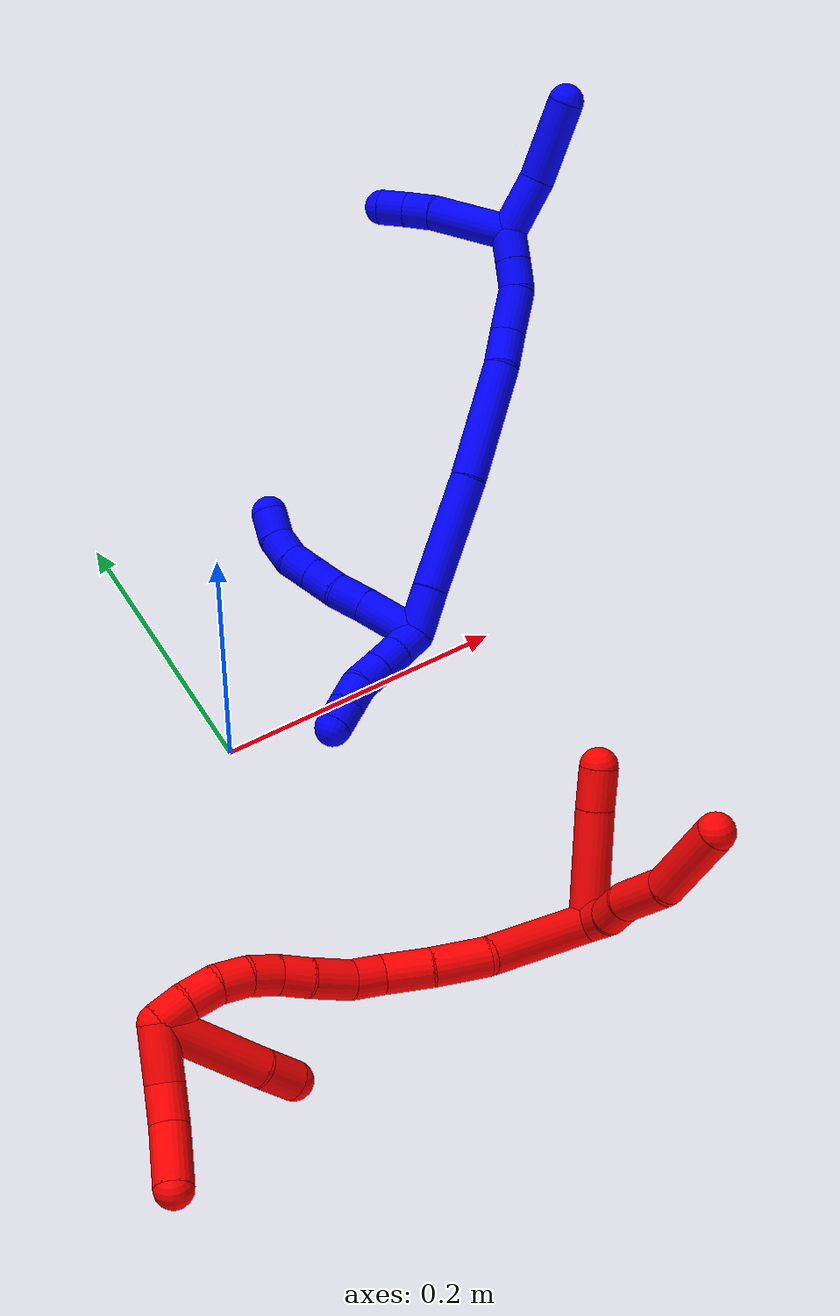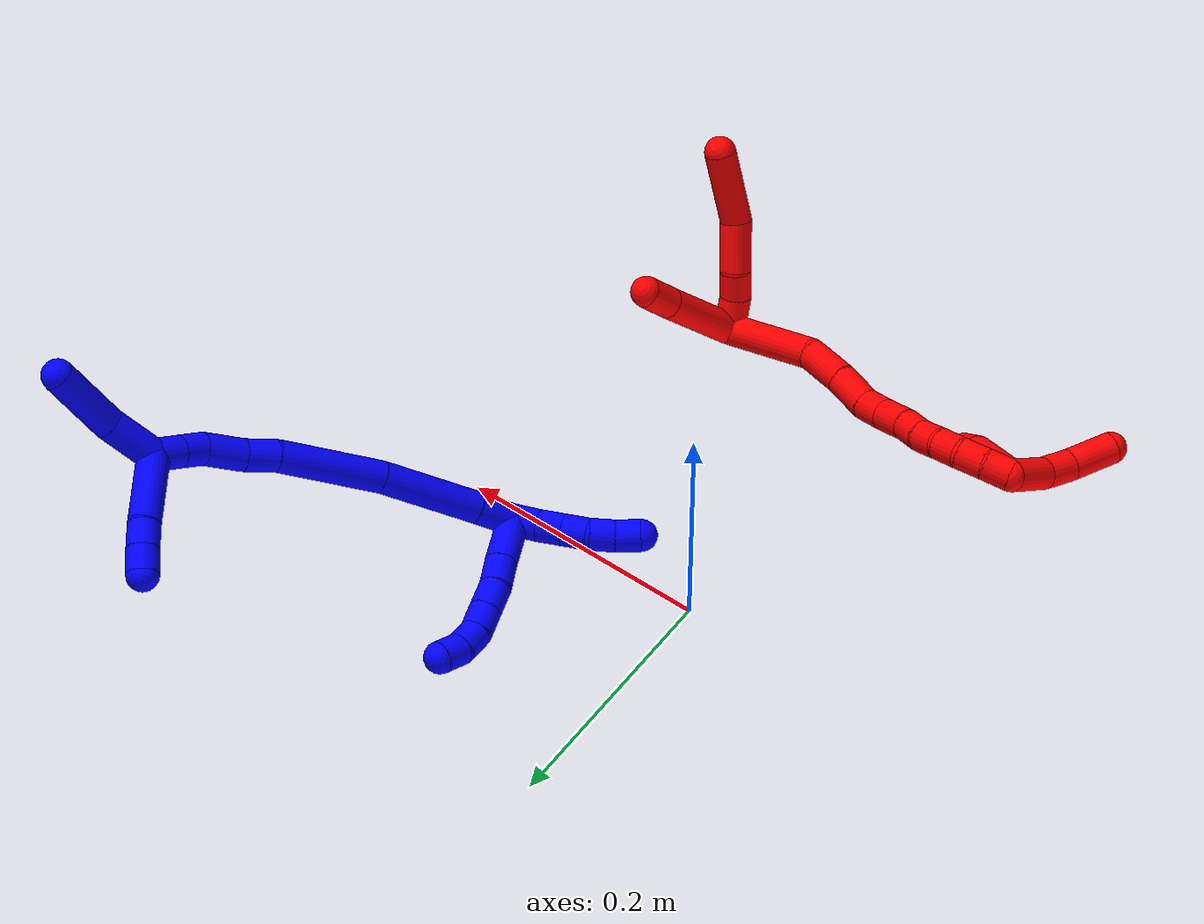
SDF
<sdf version="1.7">
 <world name="default">
  <plugin name="TubeGeneratorPlugin" filename="libtube_generator_plugin.so"/>
  <model name="photoneo_s_sensor">
   <static>1</static>
   <pose>0 0 2 1.57079 1.57079 3.14159</pose>
   <link name="link">
    <inertial><mass>0.1</mass></inertial>
    <sensor name="sensor" type="depth">
     <update_rate>30</update_rate>
     <camera>
      <horizontal_fov>1.22</horizontal_fov>
      <image><width>1920</width><height>1200</height><format>B8G8R8</format></image>
      <clip><near>0.1</near><far>4</far></clip>
      <depth_camera><output>points</output></depth_camera>
     </camera>
     <plugin name="camera_plugin" filename="libgazebo_ros_depth_camera.so">
      <baseline>0.2</baseline>
      <alwaysOn>1</alwaysOn>
      <updateRate>0.0</updateRate>
      <cameraName>camera_ir</cameraName>
      <imageTopicName>/camera/color/image_raw</imageTopicName>
      <cameraInfoTopicName>/camera/color/camera_info</cameraInfoTopicName>
      <depthImageTopicName>/camera/depth/image_raw</depthImageTopicName>
      <depthImageCameraInfoTopicName>/camera/depth/camera_info</depthImageCameraInfoTopicName>
      <pointCloudTopicName>/camera/depth/points</pointCloudTopicName>
      <frameName>fr_optical</frameName>
      <pointCloudCutoff>0.1</pointCloudCutoff>
      <pointCloudCutoffMax>2.0</pointCloudCutoffMax>
      <distortionK1>0</distortionK1>
      <distortionK2>0</distortionK2>
      <distortionK3>0</distortionK3>
      <distortionT1>0</distortionT1>
      <distortionT2>0</distortionT2>
      <CxPrime>0</CxPrime>
      <Cx>0</Cx>
      <Cy>0</Cy>
      <focalLength>0</focalLength>
      <hackBaseline>0</hackBaseline>
     </plugin>
    </sensor>
   </link>
  </model>
  <gravity>0 0 -9.8</gravity>
  <magnetic_field>6e-06 2.3e-05 -4.2e-05</magnetic_field>
  <atmosphere type="adiabatic"/>
  <physics name="default_physics" default="0" type="ode">
   <max_step_size>0.003</max_step_size>
   <real_time_factor>1</real_time_factor>
   <real_time_update_rate>1000</real_time_update_rate>
   <max_contacts>10000</max_contacts>
   <ode>
    <solver>
     <type>quick</type>
     <iters>100</iters>
     <sor>1.3</sor>
     <use_dynamic_moi_rescaling>0</use_dynamic_moi_rescaling>
    </solver>
    <constraints>
     <contact_max_correcting_vel>0</contact_max_correcting_vel>
     <contact_surface_layer>0.001</contact_surface_layer>
     <cfm>0</cfm>
     <erp>0.2</erp>
    </constraints>
   </ode>
  </physics>
  <scene><ambient>0.4 0.4 0.4 1</ambient><background>0.7 0.7 0.7 1</background><shadows>0</shadows></scene>
  <audio><device>default</device></audio>
  <spherical_coordinates>
   <surface_model>EARTH_WGS84</surface_model>
   <latitude_deg>0</latitude_deg>
   <longitude_deg>0</longitude_deg>
   <elevation>0</elevation>
   <heading_deg>0</heading_deg>
  </spherical_coordinates>
  <model name="bin">
   <static>1</static>
   <link name="bottom">
    <collision name="collision-bottom">
     <pose>0 0 -0.01 0 -0 0</pose>
     <geometry><box><size>0.8 0.6 0.02</size></box></geometry>
     <surface>
      <friction><ode><mu>100</mu><mu2>100</mu2></ode></friction>
      <contact><collide_bitmask>65535</collide_bitmask></contact>
     </surface>
    </collision>
   </link>
   <link name="west_wall">
    <collision name="collision-west_wall">
     <pose>-0.41 0 0.1 0 -0 0</pose>
     <geometry><box><size>0.02 0.6 0.2</size></box></geometry>
     <surface>
      <friction><ode><mu>100</mu><mu2>100</mu2></ode></friction>
      <contact><collide_bitmask>65535</collide_bitmask></contact>
     </surface>
    </collision>
   </link>
   <link name="east_wall">
    <collision name="collision-east_wall">
     <pose>0.41 0 0.1 0 -0 0</pose>
     <geometry><box><size>0.02 0.6 0.2</size></box></geometry>
     <surface>
      <friction><ode><mu>100</mu><mu2>100</mu2></ode></friction>
      <contact><collide_bitmask>65535</collide_bitmask></contact>
     </surface>
    </collision>
   </link>
   <link name="south_wall">
    <collision name="collision-south_wall">
     <pose>0 -0.31 0.1 0 -0 0</pose>
     <geometry><box><size>0.8 0.02 0.2</size></box></geometry>
     <surface>
      <friction><ode><mu>100</mu><mu2>100</mu2></ode></friction>
      <contact><collide_bitmask>65535</collide_bitmask></contact>
     </surface>
    </collision>
   </link>
   <link name="north_wall">
    <collision name="collision-north_wall">
     <pose>0 0.31 0.1 0 -0 0</pose>
     <geometry><box><size>0.8 0.02 0.2</size></box></geometry>
     <surface>
      <friction><ode><mu>100</mu><mu2>100</mu2></ode></friction>
      <contact><collide_bitmask>65535</collide_bitmask></contact>
     </surface>
    </collision>
   </link>
  </model>
  <model name="1">
   <static>0</static>
   <link name="1">
    <collision name="collision-cylinder-e_1_2_8">
     <pose>-0.005005 0.020351 0.004616 -1.34775 -0.23539 0.188293</pose>
     <geometry><cylinder><radius>0.0125</radius><length>0.042918</length></cylinder></geometry>
     <surface>
      <friction><ode><mu>1.16</mu><mu2>1.16</mu2><slip1>0</slip1><slip2>0</slip2></ode></friction>
      <contact><ode><kp>1e+06</kp><kd>1</kd><max_vel>0</max_vel><min_depth>0.001</min_depth></ode></contact>
     </surface>
    </collision>
    <visual name="visual-cylinder-e_1_2_8">
     <pose>-0.005005 0.020351 0.004616 -1.34775 -0.23539 0.188293</pose>
     <geometry><cylinder><radius>0.0125</radius><length>0.042918</length></cylinder></geometry>
     <material><ambient>0 0 1 1</ambient></material>
    </visual>
    <collision name="collision-cylinder-e_2_8_9">
     <pose>-0.013042 0.051818 0.011293 -1.38749 -0.262066 0.218332</pose>
     <geometry><cylinder><radius>0.0125</radius><length>0.023411</length></cylinder></geometry>
     <surface>
      <friction><ode><mu>1.16</mu><mu2>1.16</mu2><slip1>0</slip1><slip2>0</slip2></ode></friction>
      <contact><ode><kp>1e+06</kp><kd>1</kd><max_vel>0</max_vel><min_depth>0.001</min_depth></ode></contact>
     </surface>
    </collision>
    <visual name="visual-cylinder-e_2_8_9">
     <pose>-0.013042 0.051818 0.011293 -1.38749 -0.262066 0.218332</pose>
     <geometry><cylinder><radius>0.0125</radius><length>0.023411</length></cylinder></geometry>
     <material><ambient>0 0 1 1</ambient></material>
    </visual>
    <collision name="collision-cylinder-e_3_9_10">
     <pose>-0.017332 0.073625 0.016569 -1.27865 -0.112105 0.083389</pose>
     <geometry><cylinder><radius>0.0125</radius><length>0.022468</length></cylinder></geometry>
     <surface>
      <friction><ode><mu>1.16</mu><mu2>1.16</mu2><slip1>0</slip1><slip2>0</slip2></ode></friction>
      <contact><ode><kp>1e+06</kp><kd>1</kd><max_vel>0</max_vel><min_depth>0.001</min_depth></ode></contact>
     </surface>
    </collision>
    <visual name="visual-cylinder-e_3_9_10">
     <pose>-0.017332 0.073625 0.016569 -1.27865 -0.112105 0.083389</pose>
     <geometry><cylinder><radius>0.0125</radius><length>0.022468</length></cylinder></geometry>
     <material><ambient>0 0 1 1</ambient></material>
    </visual>
    <collision name="collision-cylinder-e_4_10_11">
     <pose>-0.020062 0.094269 0.022752 -1.28101 -0.14095 0.105132</pose>
     <geometry><cylinder><radius>0.0125</radius><length>0.020981</length></cylinder></geometry>
     <surface>
      <friction><ode><mu>1.16</mu><mu2>1.16</mu2><slip1>0</slip1><slip2>0</slip2></ode></friction>
      <contact><ode><kp>1e+06</kp><kd>1</kd><max_vel>0</max_vel><min_depth>0.001</min_depth></ode></contact>
     </surface>
    </collision>
    <visual name="visual-cylinder-e_4_10_11">
     <pose>-0.020062 0.094269 0.022752 -1.28101 -0.14095 0.105132</pose>
     <geometry><cylinder><radius>0.0125</radius><length>0.020981</length></cylinder></geometry>
     <material><ambient>0 0 1 1</ambient></material>
    </visual>
    <collision name="collision-cylinder-e_5_11_12">
     <pose>-0.022514 0.112516 0.031258 -0.982028 -0.097739 0.05229</pose>
     <geometry><cylinder><radius>0.0125</radius><length>0.02004</length></cylinder></geometry>
     <surface>
      <friction><ode><mu>1.16</mu><mu2>1.16</mu2><slip1>0</slip1><slip2>0</slip2></ode></friction>
      <contact><ode><kp>1e+06</kp><kd>1</kd><max_vel>0</max_vel><min_depth>0.001</min_depth></ode></contact>
     </surface>
    </collision>
    <visual name="visual-cylinder-e_5_11_12">
     <pose>-0.022514 0.112516 0.031258 -0.982028 -0.097739 0.05229</pose>
     <geometry><cylinder><radius>0.0125</radius><length>0.02004</length></cylinder></geometry>
     <material><ambient>0 0 1 1</ambient></material>
    </visual>
    <collision name="collision-cylinder-e_6_12_6">
     <pose>-0.024307 0.126868 0.044823 -0.646647 -0.08094 0.027135</pose>
     <geometry><cylinder><radius>0.0125</radius><length>0.02018</length></cylinder></geometry>
     <surface>
      <friction><ode><mu>1.16</mu><mu2>1.16</mu2><slip1>0</slip1><slip2>0</slip2></ode></friction>
      <contact><ode><kp>1e+06</kp><kd>1</kd><max_vel>0</max_vel><min_depth>0.001</min_depth></ode></contact>
     </surface>
    </collision>
    <visual name="visual-cylinder-e_6_12_6">
     <pose>-0.024307 0.126868 0.044823 -0.646647 -0.08094 0.027135</pose>
     <geometry><cylinder><radius>0.0125</radius><length>0.02018</length></cylinder></geometry>
     <material><ambient>0 0 1 1</ambient></material>
    </visual>
    <collision name="collision-cylinder-e_1_2_13">
     <pose>-0.005603 0.001327 -0.008176 -2.98065 -0.594693 2.62691</pose>
     <geometry><cylinder><radius>0.0125</radius><length>0.02</length></cylinder></geometry>
     <surface>
      <friction><ode><mu>1.16</mu><mu2>1.16</mu2><slip1>0</slip1><slip2>0</slip2></ode></friction>
      <contact><ode><kp>1e+06</kp><kd>1</kd><max_vel>0</max_vel><min_depth>0.001</min_depth></ode></contact>
     </surface>
    </collision>
    <visual name="visual-cylinder-e_1_2_13">
     <pose>-0.005603 0.001327 -0.008176 -2.98065 -0.594693 2.62691</pose>
     <geometry><cylinder><radius>0.0125</radius><length>0.02</length></cylinder></geometry>
     <material><ambient>0 0 1 1</ambient></material>
    </visual>
    <collision name="collision-cylinder-e_2_13_14">
     <pose>-0.017296 0.003598 -0.024227 -3.0224 -0.654957 2.79387</pose>
     <geometry><cylinder><radius>0.0125</radius><length>0.02</length></cylinder></geometry>
     <surface>
      <friction><ode><mu>1.16</mu><mu2>1.16</mu2><slip1>0</slip1><slip2>0</slip2></ode></friction>
      <contact><ode><kp>1e+06</kp><kd>1</kd><max_vel>0</max_vel><min_depth>0.001</min_depth></ode></contact>
     </surface>
    </collision>
    <visual name="visual-cylinder-e_2_13_14">
     <pose>-0.017296 0.003598 -0.024227 -3.0224 -0.654957 2.79387</pose>
     <geometry><cylinder><radius>0.0125</radius><length>0.02</length></cylinder></geometry>
     <material><ambient>0 0 1 1</ambient></material>
    </visual>
    <collision name="collision-cylinder-e_3_14_15">
     <pose>-0.029593 0.005589 -0.039873 -3.00759 -0.669374 2.76037</pose>
     <geometry><cylinder><radius>0.0125</radius><length>0.02</length></cylinder></geometry>
     <surface>
      <friction><ode><mu>1.16</mu><mu2>1.16</mu2><slip1>0</slip1><slip2>0</slip2></ode></friction>
      <contact><ode><kp>1e+06</kp><kd>1</kd><max_vel>0</max_vel><min_depth>0.001</min_depth></ode></contact>
     </surface>
    </collision>
    <visual name="visual-cylinder-e_3_14_15">
     <pose>-0.029593 0.005589 -0.039873 -3.00759 -0.669374 2.76037</pose>
     <geometry><cylinder><radius>0.0125</radius><length>0.02</length></cylinder></geometry>
     <material><ambient>0 0 1 1</ambient></material>
    </visual>
    <collision name="collision-cylinder-e_4_15_16">
     <pose>-0.040192 0.005795 -0.056588 3.04781 -0.454936 -2.74158</pose>
     <geometry><cylinder><radius>0.0125</radius><length>0.02</length></cylinder></geometry>
     <surface>
      <friction><ode><mu>1.16</mu><mu2>1.16</mu2><slip1>0</slip1><slip2>0</slip2></ode></friction>
      <contact><ode><kp>1e+06</kp><kd>1</kd><max_vel>0</max_vel><min_depth>0.001</min_depth></ode></contact>
     </surface>
    </collision>
    <visual name="visual-cylinder-e_4_15_16">
     <pose>-0.040192 0.005795 -0.056588 3.04781 -0.454936 -2.74158</pose>
     <geometry><cylinder><radius>0.0125</radius><length>0.02</length></cylinder></geometry>
     <material><ambient>0 0 1 1</ambient></material>
    </visual>
    <collision name="collision-cylinder-e_5_16_5">
     <pose>-0.049784 0.003493 -0.073949 2.96975 -0.546641 -2.5454</pose>
     <geometry><cylinder><radius>0.0125</radius><length>0.02</length></cylinder></geometry>
     <surface>
      <friction><ode><mu>1.16</mu><mu2>1.16</mu2><slip1>0</slip1><slip2>0</slip2></ode></friction>
      <contact><ode><kp>1e+06</kp><kd>1</kd><max_vel>0</max_vel><min_depth>0.001</min_depth></ode></contact>
     </surface>
    </collision>
    <visual name="visual-cylinder-e_5_16_5">
     <pose>-0.049784 0.003493 -0.073949 2.96975 -0.546641 -2.5454</pose>
     <geometry><cylinder><radius>0.0125</radius><length>0.02</length></cylinder></geometry>
     <material><ambient>0 0 1 1</ambient></material>
    </visual>
    <collision name="collision-cylinder-e_1_2_17">
     <pose>-0.000653 6.8e-05 0.016253 -0.004171 -0.04013 8.4e-05</pose>
     <geometry><cylinder><radius>0.0125</radius><length>0.032532</length></cylinder></geometry>
     <surface>
      <friction><ode><mu>1.16</mu><mu2>1.16</mu2><slip1>0</slip1><slip2>0</slip2></ode></friction>
      <contact><ode><kp>1e+06</kp><kd>1</kd><max_vel>0</max_vel><min_depth>0.001</min_depth></ode></contact>
     </surface>
    </collision>
    <visual name="visual-cylinder-e_1_2_17">
     <pose>-0.000653 6.8e-05 0.016253 -0.004171 -0.04013 8.4e-05</pose>
     <geometry><cylinder><radius>0.0125</radius><length>0.032532</length></cylinder></geometry>
     <material><ambient>0 0 1 1</ambient></material>
    </visual>
    <collision name="collision-cylinder-e_2_17_18">
     <pose>-0.001164 0.000195 0.073056 -0.001455 0.003479 -3e-06</pose>
     <geometry><cylinder><radius>0.0125</radius><length>0.081103</length></cylinder></geometry>
     <surface>
      <friction><ode><mu>1.16</mu><mu2>1.16</mu2><slip1>0</slip1><slip2>0</slip2></ode></friction>
      <contact><ode><kp>1e+06</kp><kd>1</kd><max_vel>0</max_vel><min_depth>0.001</min_depth></ode></contact>
     </surface>
    </collision>
    <visual name="visual-cylinder-e_2_17_18">
     <pose>-0.001164 0.000195 0.073056 -0.001455 0.003479 -3e-06</pose>
     <geometry><cylinder><radius>0.0125</radius><length>0.081103</length></cylinder></geometry>
     <material><ambient>0 0 1 1</ambient></material>
    </visual>
    <collision name="collision-cylinder-e_3_18_19">
     <pose>0.001348 0.00405 0.155512 -0.090339 0.056292 -0.002545</pose>
     <geometry><cylinder><radius>0.0125</radius><length>0.084284</length></cylinder></geometry>
     <surface>
      <friction><ode><mu>1.16</mu><mu2>1.16</mu2><slip1>0</slip1><slip2>0</slip2></ode></friction>
      <contact><ode><kp>1e+06</kp><kd>1</kd><max_vel>0</max_vel><min_depth>0.001</min_depth></ode></contact>
     </surface>
    </collision>
    <visual name="visual-cylinder-e_3_18_19">
     <pose>0.001348 0.00405 0.155512 -0.090339 0.056292 -0.002545</pose>
     <geometry><cylinder><radius>0.0125</radius><length>0.084284</length></cylinder></geometry>
     <material><ambient>0 0 1 1</ambient></material>
    </visual>
    <collision name="collision-cylinder-e_4_19_20">
     <pose>0.005504 0.010981 0.209713 -0.24964 0.139749 -0.017563</pose>
     <geometry><cylinder><radius>0.0125</radius><length>0.025632</length></cylinder></geometry>
     <surface>
      <friction><ode><mu>1.16</mu><mu2>1.16</mu2><slip1>0</slip1><slip2>0</slip2></ode></friction>
      <contact><ode><kp>1e+06</kp><kd>1</kd><max_vel>0</max_vel><min_depth>0.001</min_depth></ode></contact>
     </surface>
    </collision>
    <visual name="visual-cylinder-e_4_19_20">
     <pose>0.005504 0.010981 0.209713 -0.24964 0.139749 -0.017563</pose>
     <geometry><cylinder><radius>0.0125</radius><length>0.025632</length></cylinder></geometry>
     <material><ambient>0 0 1 1</ambient></material>
    </visual>
    <collision name="collision-cylinder-e_5_20_21">
     <pose>0.007493 0.016593 0.238374 -0.150215 0.012289 -0.000925</pose>
     <geometry><cylinder><radius>0.0125</radius><length>0.033102</length></cylinder></geometry>
     <surface>
      <friction><ode><mu>1.16</mu><mu2>1.16</mu2><slip1>0</slip1><slip2>0</slip2></ode></friction>
      <contact><ode><kp>1e+06</kp><kd>1</kd><max_vel>0</max_vel><min_depth>0.001</min_depth></ode></contact>
     </surface>
    </collision>
    <visual name="visual-cylinder-e_5_20_21">
     <pose>0.007493 0.016593 0.238374 -0.150215 0.012289 -0.000925</pose>
     <geometry><cylinder><radius>0.0125</radius><length>0.033102</length></cylinder></geometry>
     <material><ambient>0 0 1 1</ambient></material>
    </visual>
    <collision name="collision-cylinder-e_6_21_22">
     <pose>0.006394 0.023511 0.263935 -0.449819 -0.126805 0.029047</pose>
     <geometry><cylinder><radius>0.0125</radius><length>0.020594</length></cylinder></geometry>
     <surface>
      <friction><ode><mu>1.16</mu><mu2>1.16</mu2><slip1>0</slip1><slip2>0</slip2></ode></friction>
      <contact><ode><kp>1e+06</kp><kd>1</kd><max_vel>0</max_vel><min_depth>0.001</min_depth></ode></contact>
     </surface>
    </collision>
    <visual name="visual-cylinder-e_6_21_22">
     <pose>0.006394 0.023511 0.263935 -0.449819 -0.126805 0.029047</pose>
     <geometry><cylinder><radius>0.0125</radius><length>0.020594</length></cylinder></geometry>
     <material><ambient>0 0 1 1</ambient></material>
    </visual>
    <collision name="collision-cylinder-e_7_22_1">
     <pose>0.003544 0.032939 0.283241 -0.458321 -0.136436 0.031872</pose>
     <geometry><cylinder><radius>0.0125</radius><length>0.022754</length></cylinder></geometry>
     <surface>
      <friction><ode><mu>1.16</mu><mu2>1.16</mu2><slip1>0</slip1><slip2>0</slip2></ode></friction>
      <contact><ode><kp>1e+06</kp><kd>1</kd><max_vel>0</max_vel><min_depth>0.001</min_depth></ode></contact>
     </surface>
    </collision>
    <visual name="visual-cylinder-e_7_22_1">
     <pose>0.003544 0.032939 0.283241 -0.458321 -0.136436 0.031872</pose>
     <geometry><cylinder><radius>0.0125</radius><length>0.022754</length></cylinder></geometry>
     <material><ambient>0 0 1 1</ambient></material>
    </visual>
    <collision name="collision-cylinder-e_1_1_23">
     <pose>-0.003954 0.066795 0.294094 -1.545 -0.203219 0.198077</pose>
     <geometry><cylinder><radius>0.0125</radius><length>0.058973</length></cylinder></geometry>
     <surface>
      <friction><ode><mu>1.16</mu><mu2>1.16</mu2><slip1>0</slip1><slip2>0</slip2></ode></friction>
      <contact><ode><kp>1e+06</kp><kd>1</kd><max_vel>0</max_vel><min_depth>0.001</min_depth></ode></contact>
     </surface>
    </collision>
    <visual name="visual-cylinder-e_1_1_23">
     <pose>-0.003954 0.066795 0.294094 -1.545 -0.203219 0.198077</pose>
     <geometry><cylinder><radius>0.0125</radius><length>0.058973</length></cylinder></geometry>
     <material><ambient>0 0 1 1</ambient></material>
    </visual>
    <collision name="collision-cylinder-e_2_23_24">
     <pose>-0.011222 0.105776 0.294041 -1.64952 -0.129118 0.139672</pose>
     <geometry><cylinder><radius>0.0125</radius><length>0.020455</length></cylinder></geometry>
     <surface>
      <friction><ode><mu>1.16</mu><mu2>1.16</mu2><slip1>0</slip1><slip2>0</slip2></ode></friction>
      <contact><ode><kp>1e+06</kp><kd>1</kd><max_vel>0</max_vel><min_depth>0.001</min_depth></ode></contact>
     </surface>
    </collision>
    <visual name="visual-cylinder-e_2_23_24">
     <pose>-0.011222 0.105776 0.294041 -1.64952 -0.129118 0.139672</pose>
     <geometry><cylinder><radius>0.0125</radius><length>0.020455</length></cylinder></geometry>
     <material><ambient>0 0 1 1</ambient></material>
    </visual>
    <collision name="collision-cylinder-e_3_24_4">
     <pose>-0.014195 0.125968 0.292041 -1.6895 -0.161679 0.182001</pose>
     <geometry><cylinder><radius>0.0125</radius><length>0.020573</length></cylinder></geometry>
     <surface>
      <friction><ode><mu>1.16</mu><mu2>1.16</mu2><slip1>0</slip1><slip2>0</slip2></ode></friction>
      <contact><ode><kp>1e+06</kp><kd>1</kd><max_vel>0</max_vel><min_depth>0.001</min_depth></ode></contact>
     </surface>
    </collision>
    <visual name="visual-cylinder-e_3_24_4">
     <pose>-0.014195 0.125968 0.292041 -1.6895 -0.161679 0.182001</pose>
     <geometry><cylinder><radius>0.0125</radius><length>0.020573</length></cylinder></geometry>
     <material><ambient>0 0 1 1</ambient></material>
    </visual>
    <collision name="collision-cylinder-e_1_1_25">
     <pose>-0.000349 0.032392 0.313454 0.268566 -0.11203 -0.01515</pose>
     <geometry><cylinder><radius>0.0125</radius><length>0.041969</length></cylinder></geometry>
     <surface>
      <friction><ode><mu>1.16</mu><mu2>1.16</mu2><slip1>0</slip1><slip2>0</slip2></ode></friction>
      <contact><ode><kp>1e+06</kp><kd>1</kd><max_vel>0</max_vel><min_depth>0.001</min_depth></ode></contact>
     </surface>
    </collision>
    <visual name="visual-cylinder-e_1_1_25">
     <pose>-0.000349 0.032392 0.313454 0.268566 -0.11203 -0.01515</pose>
     <geometry><cylinder><radius>0.0125</radius><length>0.041969</length></cylinder></geometry>
     <material><ambient>0 0 1 1</ambient></material>
    </visual>
    <collision name="collision-cylinder-e_2_25_3">
     <pose>-0.013059 0.019188 0.359553 0.286955 -0.36524 -0.053348</pose>
     <geometry><cylinder><radius>0.0125</radius><length>0.058031</length></cylinder></geometry>
     <surface>
      <friction><ode><mu>1.16</mu><mu2>1.16</mu2><slip1>0</slip1><slip2>0</slip2></ode></friction>
      <contact><ode><kp>1e+06</kp><kd>1</kd><max_vel>0</max_vel><min_depth>0.001</min_depth></ode></contact>
     </surface>
    </collision>
    <visual name="visual-cylinder-e_2_25_3">
     <pose>-0.013059 0.019188 0.359553 0.286955 -0.36524 -0.053348</pose>
     <geometry><cylinder><radius>0.0125</radius><length>0.058031</length></cylinder></geometry>
     <material><ambient>0 0 1 1</ambient></material>
    </visual>
    <collision name="collision-sphere-3">
     <pose>-0.023422 0.011518 0.385547 0 -0 0</pose>
     <geometry><sphere><radius>0.0125</radius></sphere></geometry>
     <surface>
      <friction><ode><mu>1.16</mu><mu2>1.16</mu2><slip1>0</slip1><slip2>0</slip2></ode></friction>
      <contact><ode><kp>1e+06</kp><kd>1</kd><max_vel>0</max_vel><min_depth>0.001</min_depth></ode></contact>
     </surface>
    </collision>
    <visual name="visual-sphere-3">
     <pose>-0.023422 0.011518 0.385547 0 -0 0</pose>
     <geometry><sphere><radius>0.0125</radius></sphere></geometry>
     <material><ambient>0 0 1 1</ambient></material>
    </visual>
    <collision name="collision-sphere-25">
     <pose>-0.002695 0.026859 0.333559 0 -0 0</pose>
     <geometry><sphere><radius>0.0125</radius></sphere></geometry>
     <surface>
      <friction><ode><mu>1.16</mu><mu2>1.16</mu2><slip1>0</slip1><slip2>0</slip2></ode></friction>
      <contact><ode><kp>1e+06</kp><kd>1</kd><max_vel>0</max_vel><min_depth>0.001</min_depth></ode></contact>
     </surface>
    </collision>
    <visual name="visual-sphere-25">
     <pose>-0.002695 0.026859 0.333559 0 -0 0</pose>
     <geometry><sphere><radius>0.0125</radius></sphere></geometry>
     <material><ambient>0 0 1 1</ambient></material>
    </visual>
    <collision name="collision-sphere-4">
     <pose>-0.01585 0.136048 0.290839 0 -0 0</pose>
     <geometry><sphere><radius>0.0125</radius></sphere></geometry>
     <surface>
      <friction><ode><mu>1.16</mu><mu2>1.16</mu2><slip1>0</slip1><slip2>0</slip2></ode></friction>
      <contact><ode><kp>1e+06</kp><kd>1</kd><max_vel>0</max_vel><min_depth>0.001</min_depth></ode></contact>
     </surface>
    </collision>
    <visual name="visual-sphere-4">
     <pose>-0.01585 0.136048 0.290839 0 -0 0</pose>
     <geometry><sphere><radius>0.0125</radius></sphere></geometry>
     <material><ambient>0 0 1 1</ambient></material>
    </visual>
    <collision name="collision-sphere-24">
     <pose>-0.012539 0.115887 0.293244 0 -0 0</pose>
     <geometry><sphere><radius>0.0125</radius></sphere></geometry>
     <surface>
      <friction><ode><mu>1.16</mu><mu2>1.16</mu2><slip1>0</slip1><slip2>0</slip2></ode></friction>
      <contact><ode><kp>1e+06</kp><kd>1</kd><max_vel>0</max_vel><min_depth>0.001</min_depth></ode></contact>
     </surface>
    </collision>
    <visual name="visual-sphere-24">
     <pose>-0.012539 0.115887 0.293244 0 -0 0</pose>
     <geometry><sphere><radius>0.0125</radius></sphere></geometry>
     <material><ambient>0 0 1 1</ambient></material>
    </visual>
    <collision name="collision-sphere-23">
     <pose>-0.009905 0.095665 0.294839 0 -0 0</pose>
     <geometry><sphere><radius>0.0125</radius></sphere></geometry>
     <surface>
      <friction><ode><mu>1.16</mu><mu2>1.16</mu2><slip1>0</slip1><slip2>0</slip2></ode></friction>
      <contact><ode><kp>1e+06</kp><kd>1</kd><max_vel>0</max_vel><min_depth>0.001</min_depth></ode></contact>
     </surface>
    </collision>
    <visual name="visual-sphere-23">
     <pose>-0.009905 0.095665 0.294839 0 -0 0</pose>
     <geometry><sphere><radius>0.0125</radius></sphere></geometry>
     <material><ambient>0 0 1 1</ambient></material>
    </visual>
    <collision name="collision-sphere-1">
     <pose>0.001997 0.037925 0.293349 0 -0 0</pose>
     <geometry><sphere><radius>0.0125</radius></sphere></geometry>
     <surface>
      <friction><ode><mu>1.16</mu><mu2>1.16</mu2><slip1>0</slip1><slip2>0</slip2></ode></friction>
      <contact><ode><kp>1e+06</kp><kd>1</kd><max_vel>0</max_vel><min_depth>0.001</min_depth></ode></contact>
     </surface>
    </collision>
    <visual name="visual-sphere-1">
     <pose>0.001997 0.037925 0.293349 0 -0 0</pose>
     <geometry><sphere><radius>0.0125</radius></sphere></geometry>
     <material><ambient>0 0 1 1</ambient></material>
    </visual>
    <collision name="collision-sphere-22">
     <pose>0.005092 0.027952 0.273133 0 -0 0</pose>
     <geometry><sphere><radius>0.0125</radius></sphere></geometry>
     <surface>
      <friction><ode><mu>1.16</mu><mu2>1.16</mu2><slip1>0</slip1><slip2>0</slip2></ode></friction>
      <contact><ode><kp>1e+06</kp><kd>1</kd><max_vel>0</max_vel><min_depth>0.001</min_depth></ode></contact>
     </surface>
    </collision>
    <visual name="visual-sphere-22">
     <pose>0.005092 0.027952 0.273133 0 -0 0</pose>
     <geometry><sphere><radius>0.0125</radius></sphere></geometry>
     <material><ambient>0 0 1 1</ambient></material>
    </visual>
    <collision name="collision-sphere-21">
     <pose>0.007696 0.019069 0.254737 0 -0 0</pose>
     <geometry><sphere><radius>0.0125</radius></sphere></geometry>
     <surface>
      <friction><ode><mu>1.16</mu><mu2>1.16</mu2><slip1>0</slip1><slip2>0</slip2></ode></friction>
      <contact><ode><kp>1e+06</kp><kd>1</kd><max_vel>0</max_vel><min_depth>0.001</min_depth></ode></contact>
     </surface>
    </collision>
    <visual name="visual-sphere-21">
     <pose>0.007696 0.019069 0.254737 0 -0 0</pose>
     <geometry><sphere><radius>0.0125</radius></sphere></geometry>
     <material><ambient>0 0 1 1</ambient></material>
    </visual>
    <collision name="collision-sphere-12">
     <pose>-0.023492 0.120809 0.036796 0 -0 0</pose>
     <geometry><sphere><radius>0.0125</radius></sphere></geometry>
     <surface>
      <friction><ode><mu>1.16</mu><mu2>1.16</mu2><slip1>0</slip1><slip2>0</slip2></ode></friction>
      <contact><ode><kp>1e+06</kp><kd>1</kd><max_vel>0</max_vel><min_depth>0.001</min_depth></ode></contact>
     </surface>
    </collision>
    <visual name="visual-sphere-12">
     <pose>-0.023492 0.120809 0.036796 0 -0 0</pose>
     <geometry><sphere><radius>0.0125</radius></sphere></geometry>
     <material><ambient>0 0 1 1</ambient></material>
    </visual>
    <collision name="collision-sphere-11">
     <pose>-0.021536 0.104222 0.02572 0 -0 0</pose>
     <geometry><sphere><radius>0.0125</radius></sphere></geometry>
     <surface>
      <friction><ode><mu>1.16</mu><mu2>1.16</mu2><slip1>0</slip1><slip2>0</slip2></ode></friction>
      <contact><ode><kp>1e+06</kp><kd>1</kd><max_vel>0</max_vel><min_depth>0.001</min_depth></ode></contact>
     </surface>
    </collision>
    <visual name="visual-sphere-11">
     <pose>-0.021536 0.104222 0.02572 0 -0 0</pose>
     <geometry><sphere><radius>0.0125</radius></sphere></geometry>
     <material><ambient>0 0 1 1</ambient></material>
    </visual>
    <collision name="collision-sphere-10">
     <pose>-0.018588 0.084315 0.019784 0 -0 0</pose>
     <geometry><sphere><radius>0.0125</radius></sphere></geometry>
     <surface>
      <friction><ode><mu>1.16</mu><mu2>1.16</mu2><slip1>0</slip1><slip2>0</slip2></ode></friction>
      <contact><ode><kp>1e+06</kp><kd>1</kd><max_vel>0</max_vel><min_depth>0.001</min_depth></ode></contact>
     </surface>
    </collision>
    <visual name="visual-sphere-10">
     <pose>-0.018588 0.084315 0.019784 0 -0 0</pose>
     <geometry><sphere><radius>0.0125</radius></sphere></geometry>
     <material><ambient>0 0 1 1</ambient></material>
    </visual>
    <collision name="collision-sphere-9">
     <pose>-0.016075 0.062934 0.013354 0 -0 0</pose>
     <geometry><sphere><radius>0.0125</radius></sphere></geometry>
     <surface>
      <friction><ode><mu>1.16</mu><mu2>1.16</mu2><slip1>0</slip1><slip2>0</slip2></ode></friction>
      <contact><ode><kp>1e+06</kp><kd>1</kd><max_vel>0</max_vel><min_depth>0.001</min_depth></ode></contact>
     </surface>
    </collision>
    <visual name="visual-sphere-9">
     <pose>-0.016075 0.062934 0.013354 0 -0 0</pose>
     <geometry><sphere><radius>0.0125</radius></sphere></geometry>
     <material><ambient>0 0 1 1</ambient></material>
    </visual>
    <collision name="collision-sphere-2">
     <geometry><sphere><radius>0.0125</radius></sphere></geometry>
     <surface>
      <friction><ode><mu>1.16</mu><mu2>1.16</mu2><slip1>0</slip1><slip2>0</slip2></ode></friction>
      <contact><ode><kp>1e+06</kp><kd>1</kd><max_vel>0</max_vel><min_depth>0.001</min_depth></ode></contact>
     </surface>
    </collision>
    <visual name="visual-sphere-2">
     <geometry><sphere><radius>0.0125</radius></sphere></geometry>
     <material><ambient>0 0 1 1</ambient></material>
    </visual>
    <collision name="collision-sphere-19">
     <pose>0.003719 0.007845 0.197416 0 -0 0</pose>
     <geometry><sphere><radius>0.0125</radius></sphere></geometry>
     <surface>
      <friction><ode><mu>1.16</mu><mu2>1.16</mu2><slip1>0</slip1><slip2>0</slip2></ode></friction>
      <contact><ode><kp>1e+06</kp><kd>1</kd><max_vel>0</max_vel><min_depth>0.001</min_depth></ode></contact>
     </surface>
    </collision>
    <visual name="visual-sphere-19">
     <pose>0.003719 0.007845 0.197416 0 -0 0</pose>
     <geometry><sphere><radius>0.0125</radius></sphere></geometry>
     <material><ambient>0 0 1 1</ambient></material>
    </visual>
    <collision name="collision-sphere-8">
     <pose>-0.01001 0.040701 0.009232 0 -0 0</pose>
     <geometry><sphere><radius>0.0125</radius></sphere></geometry>
     <surface>
      <friction><ode><mu>1.16</mu><mu2>1.16</mu2><slip1>0</slip1><slip2>0</slip2></ode></friction>
      <contact><ode><kp>1e+06</kp><kd>1</kd><max_vel>0</max_vel><min_depth>0.001</min_depth></ode></contact>
     </surface>
    </collision>
    <visual name="visual-sphere-8">
     <pose>-0.01001 0.040701 0.009232 0 -0 0</pose>
     <geometry><sphere><radius>0.0125</radius></sphere></geometry>
     <material><ambient>0 0 1 1</ambient></material>
    </visual>
    <collision name="collision-sphere-6">
     <pose>-0.025123 0.132928 0.05285 0 -0 0</pose>
     <geometry><sphere><radius>0.0125</radius></sphere></geometry>
     <surface>
      <friction><ode><mu>1.16</mu><mu2>1.16</mu2><slip1>0</slip1><slip2>0</slip2></ode></friction>
      <contact><ode><kp>1e+06</kp><kd>1</kd><max_vel>0</max_vel><min_depth>0.001</min_depth></ode></contact>
     </surface>
    </collision>
    <visual name="visual-sphere-6">
     <pose>-0.025123 0.132928 0.05285 0 -0 0</pose>
     <geometry><sphere><radius>0.0125</radius></sphere></geometry>
     <material><ambient>0 0 1 1</ambient></material>
    </visual>
    <collision name="collision-sphere-13">
     <pose>-0.011205 0.002655 -0.016352 0 -0 0</pose>
     <geometry><sphere><radius>0.0125</radius></sphere></geometry>
     <surface>
      <friction><ode><mu>1.16</mu><mu2>1.16</mu2><slip1>0</slip1><slip2>0</slip2></ode></friction>
      <contact><ode><kp>1e+06</kp><kd>1</kd><max_vel>0</max_vel><min_depth>0.001</min_depth></ode></contact>
     </surface>
    </collision>
    <visual name="visual-sphere-13">
     <pose>-0.011205 0.002655 -0.016352 0 -0 0</pose>
     <geometry><sphere><radius>0.0125</radius></sphere></geometry>
     <material><ambient>0 0 1 1</ambient></material>
    </visual>
    <collision name="collision-sphere-14">
     <pose>-0.023388 0.004541 -0.032101 0 -0 0</pose>
     <geometry><sphere><radius>0.0125</radius></sphere></geometry>
     <surface>
      <friction><ode><mu>1.16</mu><mu2>1.16</mu2><slip1>0</slip1><slip2>0</slip2></ode></friction>
      <contact><ode><kp>1e+06</kp><kd>1</kd><max_vel>0</max_vel><min_depth>0.001</min_depth></ode></contact>
     </surface>
    </collision>
    <visual name="visual-sphere-14">
     <pose>-0.023388 0.004541 -0.032101 0 -0 0</pose>
     <geometry><sphere><radius>0.0125</radius></sphere></geometry>
     <material><ambient>0 0 1 1</ambient></material>
    </visual>
    <collision name="collision-sphere-15">
     <pose>-0.035797 0.006636 -0.047645 0 -0 0</pose>
     <geometry><sphere><radius>0.0125</radius></sphere></geometry>
     <surface>
      <friction><ode><mu>1.16</mu><mu2>1.16</mu2><slip1>0</slip1><slip2>0</slip2></ode></friction>
      <contact><ode><kp>1e+06</kp><kd>1</kd><max_vel>0</max_vel><min_depth>0.001</min_depth></ode></contact>
     </surface>
    </collision>
    <visual name="visual-sphere-15">
     <pose>-0.035797 0.006636 -0.047645 0 -0 0</pose>
     <geometry><sphere><radius>0.0125</radius></sphere></geometry>
     <material><ambient>0 0 1 1</ambient></material>
    </visual>
    <collision name="collision-sphere-16">
     <pose>-0.044586 0.004954 -0.065532 0 -0 0</pose>
     <geometry><sphere><radius>0.0125</radius></sphere></geometry>
     <surface>
      <friction><ode><mu>1.16</mu><mu2>1.16</mu2><slip1>0</slip1><slip2>0</slip2></ode></friction>
      <contact><ode><kp>1e+06</kp><kd>1</kd><max_vel>0</max_vel><min_depth>0.001</min_depth></ode></contact>
     </surface>
    </collision>
    <visual name="visual-sphere-16">
     <pose>-0.044586 0.004954 -0.065532 0 -0 0</pose>
     <geometry><sphere><radius>0.0125</radius></sphere></geometry>
     <material><ambient>0 0 1 1</ambient></material>
    </visual>
    <collision name="collision-sphere-5">
     <pose>-0.054982 0.002032 -0.082366 0 -0 0</pose>
     <geometry><sphere><radius>0.0125</radius></sphere></geometry>
     <surface>
      <friction><ode><mu>1.16</mu><mu2>1.16</mu2><slip1>0</slip1><slip2>0</slip2></ode></friction>
      <contact><ode><kp>1e+06</kp><kd>1</kd><max_vel>0</max_vel><min_depth>0.001</min_depth></ode></contact>
     </surface>
    </collision>
    <visual name="visual-sphere-5">
     <pose>-0.054982 0.002032 -0.082366 0 -0 0</pose>
     <geometry><sphere><radius>0.0125</radius></sphere></geometry>
     <material><ambient>0 0 1 1</ambient></material>
    </visual>
    <collision name="collision-sphere-17">
     <pose>-0.001305 0.000136 0.032505 0 -0 0</pose>
     <geometry><sphere><radius>0.0125</radius></sphere></geometry>
     <surface>
      <friction><ode><mu>1.16</mu><mu2>1.16</mu2><slip1>0</slip1><slip2>0</slip2></ode></friction>
      <contact><ode><kp>1e+06</kp><kd>1</kd><max_vel>0</max_vel><min_depth>0.001</min_depth></ode></contact>
     </surface>
    </collision>
    <visual name="visual-sphere-17">
     <pose>-0.001305 0.000136 0.032505 0 -0 0</pose>
     <geometry><sphere><radius>0.0125</radius></sphere></geometry>
     <material><ambient>0 0 1 1</ambient></material>
    </visual>
    <collision name="collision-sphere-18">
     <pose>-0.001023 0.000254 0.113608 0 -0 0</pose>
     <geometry><sphere><radius>0.0125</radius></sphere></geometry>
     <surface>
      <friction><ode><mu>1.16</mu><mu2>1.16</mu2><slip1>0</slip1><slip2>0</slip2></ode></friction>
      <contact><ode><kp>1e+06</kp><kd>1</kd><max_vel>0</max_vel><min_depth>0.001</min_depth></ode></contact>
     </surface>
    </collision>
    <visual name="visual-sphere-18">
     <pose>-0.001023 0.000254 0.113608 0 -0 0</pose>
     <geometry><sphere><radius>0.0125</radius></sphere></geometry>
     <material><ambient>0 0 1 1</ambient></material>
    </visual>
    <collision name="collision-sphere-20">
     <pose>0.007289 0.014116 0.222011 0 -0 0</pose>
     <geometry><sphere><radius>0.0125</radius></sphere></geometry>
     <surface>
      <friction><ode><mu>1.16</mu><mu2>1.16</mu2><slip1>0</slip1><slip2>0</slip2></ode></friction>
      <contact><ode><kp>1e+06</kp><kd>1</kd><max_vel>0</max_vel><min_depth>0.001</min_depth></ode></contact>
     </surface>
    </collision>
    <visual name="visual-sphere-20">
     <pose>0.007289 0.014116 0.222011 0 -0 0</pose>
     <geometry><sphere><radius>0.0125</radius></sphere></geometry>
     <material><ambient>0 0 1 1</ambient></material>
    </visual>
    <inertial>
     <pose>-0.008066 0.032694 0.142508 0 -0 0</pose>
     <mass>0.75</mass>
     <inertia><ixx>0.000168</ixx><ixy>0</ixy><ixz>0</ixz><iyy>0.000178</iyy><iyz>0</iyz><izz>6e-06</izz></inertia>
    </inertial>
   </link>
   <pose>0.153216 0.017014 0.012431 -0.545478 0.955481 0.027176</pose>
  </model>
  <model name="2">
   <static>0</static>
   <link name="2">
    <collision name="collision-cylinder-e_1_2_8">
     <pose>-0.001622 0.011296 -0.007435 -2.15289 -0.119377 0.220845</pose>
     <geometry><cylinder><radius>0.0125</radius><length>0.02724</length></cylinder></geometry>
     <surface>
      <friction><ode><mu>1.16</mu><mu2>1.16</mu2><slip1>0</slip1><slip2>0</slip2></ode></friction>
      <contact><ode><kp>1e+06</kp><kd>1</kd><max_vel>0</max_vel><min_depth>0.001</min_depth></ode></contact>
     </surface>
    </collision>
    <visual name="visual-cylinder-e_1_2_8">
     <pose>-0.001622 0.011296 -0.007435 -2.15289 -0.119377 0.220845</pose>
     <geometry><cylinder><radius>0.0125</radius><length>0.02724</length></cylinder></geometry>
     <material><ambient>1 0 0 1</ambient></material>
    </visual>
    <collision name="collision-cylinder-e_2_8_9">
     <pose>-0.003539 0.030382 -0.022845 -2.36797 -0.026443 0.064899</pose>
     <geometry><cylinder><radius>0.0125</radius><length>0.022305</length></cylinder></geometry>
     <surface>
      <friction><ode><mu>1.16</mu><mu2>1.16</mu2><slip1>0</slip1><slip2>0</slip2></ode></friction>
      <contact><ode><kp>1e+06</kp><kd>1</kd><max_vel>0</max_vel><min_depth>0.001</min_depth></ode></contact>
     </surface>
    </collision>
    <visual name="visual-cylinder-e_2_8_9">
     <pose>-0.003539 0.030382 -0.022845 -2.36797 -0.026443 0.064899</pose>
     <geometry><cylinder><radius>0.0125</radius><length>0.022305</length></cylinder></geometry>
     <material><ambient>1 0 0 1</ambient></material>
    </visual>
    <collision name="collision-cylinder-e_3_9_10">
     <pose>-0.002931 0.055076 -0.041935 -2.15244 0.044594 -0.082658</pose>
     <geometry><cylinder><radius>0.0125</radius><length>0.040502</length></cylinder></geometry>
     <surface>
      <friction><ode><mu>1.16</mu><mu2>1.16</mu2><slip1>0</slip1><slip2>0</slip2></ode></friction>
      <contact><ode><kp>1e+06</kp><kd>1</kd><max_vel>0</max_vel><min_depth>0.001</min_depth></ode></contact>
     </surface>
    </collision>
    <visual name="visual-cylinder-e_3_9_10">
     <pose>-0.002931 0.055076 -0.041935 -2.15244 0.044594 -0.082658</pose>
     <geometry><cylinder><radius>0.0125</radius><length>0.040502</length></cylinder></geometry>
     <material><ambient>1 0 0 1</ambient></material>
    </visual>
    <collision name="collision-cylinder-e_4_10_6">
     <pose>0.002139 0.090491 -0.076257 -2.4683 0.139477 -0.394015</pose>
     <geometry><cylinder><radius>0.0125</radius><length>0.059953</length></cylinder></geometry>
     <surface>
      <friction><ode><mu>1.16</mu><mu2>1.16</mu2><slip1>0</slip1><slip2>0</slip2></ode></friction>
      <contact><ode><kp>1e+06</kp><kd>1</kd><max_vel>0</max_vel><min_depth>0.001</min_depth></ode></contact>
     </surface>
    </collision>
    <visual name="visual-cylinder-e_4_10_6">
     <pose>0.002139 0.090491 -0.076257 -2.4683 0.139477 -0.394015</pose>
     <geometry><cylinder><radius>0.0125</radius><length>0.059953</length></cylinder></geometry>
     <material><ambient>1 0 0 1</ambient></material>
    </visual>
    <collision name="collision-cylinder-e_1_2_11">
     <pose>0.012303 -0.004556 -0.034108 3.00881 0.343355 2.4092</pose>
     <geometry><cylinder><radius>0.0125</radius><length>0.073088</length></cylinder></geometry>
     <surface>
      <friction><ode><mu>1.16</mu><mu2>1.16</mu2><slip1>0</slip1><slip2>0</slip2></ode></friction>
      <contact><ode><kp>1e+06</kp><kd>1</kd><max_vel>0</max_vel><min_depth>0.001</min_depth></ode></contact>
     </surface>
    </collision>
    <visual name="visual-cylinder-e_1_2_11">
     <pose>0.012303 -0.004556 -0.034108 3.00881 0.343355 2.4092</pose>
     <geometry><cylinder><radius>0.0125</radius><length>0.073088</length></cylinder></geometry>
     <material><ambient>1 0 0 1</ambient></material>
    </visual>
    <collision name="collision-cylinder-e_2_11_5">
     <pose>0.029238 -0.01028 -0.080795 3.04903 0.351524 2.6314</pose>
     <geometry><cylinder><radius>0.0125</radius><length>0.026912</length></cylinder></geometry>
     <surface>
      <friction><ode><mu>1.16</mu><mu2>1.16</mu2><slip1>0</slip1><slip2>0</slip2></ode></friction>
      <contact><ode><kp>1e+06</kp><kd>1</kd><max_vel>0</max_vel><min_depth>0.001</min_depth></ode></contact>
     </surface>
    </collision>
    <visual name="visual-cylinder-e_2_11_5">
     <pose>0.029238 -0.01028 -0.080795 3.04903 0.351524 2.6314</pose>
     <geometry><cylinder><radius>0.0125</radius><length>0.026912</length></cylinder></geometry>
     <material><ambient>1 0 0 1</ambient></material>
    </visual>
    <collision name="collision-cylinder-e_1_2_12">
     <pose>-0.038725 -0.005885 -0.005056 2.28053 -1.37306 -2.12</pose>
     <geometry><cylinder><radius>0.0125</radius><length>0.07899</length></cylinder></geometry>
     <surface>
      <friction><ode><mu>1.16</mu><mu2>1.16</mu2><slip1>0</slip1><slip2>0</slip2></ode></friction>
      <contact><ode><kp>1e+06</kp><kd>1</kd><max_vel>0</max_vel><min_depth>0.001</min_depth></ode></contact>
     </surface>
    </collision>
    <visual name="visual-cylinder-e_1_2_12">
     <pose>-0.038725 -0.005885 -0.005056 2.28053 -1.37306 -2.12</pose>
     <geometry><cylinder><radius>0.0125</radius><length>0.07899</length></cylinder></geometry>
     <material><ambient>1 0 0 1</ambient></material>
    </visual>
    <collision name="collision-cylinder-e_2_12_13">
     <pose>-0.093504 -0.020109 -0.011261 1.70778 -1.08787 -1.21321</pose>
     <geometry><cylinder><radius>0.0125</radius><length>0.036252</length></cylinder></geometry>
     <surface>
      <friction><ode><mu>1.16</mu><mu2>1.16</mu2><slip1>0</slip1><slip2>0</slip2></ode></friction>
      <contact><ode><kp>1e+06</kp><kd>1</kd><max_vel>0</max_vel><min_depth>0.001</min_depth></ode></contact>
     </surface>
    </collision>
    <visual name="visual-cylinder-e_2_12_13">
     <pose>-0.093504 -0.020109 -0.011261 1.70778 -1.08787 -1.21321</pose>
     <geometry><cylinder><radius>0.0125</radius><length>0.036252</length></cylinder></geometry>
     <material><ambient>1 0 0 1</ambient></material>
    </visual>
    <collision name="collision-cylinder-e_3_13_14">
     <pose>-0.122633 -0.037024 -0.013314 1.6758 -0.987737 -1.07802</pose>
     <geometry><cylinder><radius>0.0125</radius><length>0.031327</length></cylinder></geometry>
     <surface>
      <friction><ode><mu>1.16</mu><mu2>1.16</mu2><slip1>0</slip1><slip2>0</slip2></ode></friction>
      <contact><ode><kp>1e+06</kp><kd>1</kd><max_vel>0</max_vel><min_depth>0.001</min_depth></ode></contact>
     </surface>
    </collision>
    <visual name="visual-cylinder-e_3_13_14">
     <pose>-0.122633 -0.037024 -0.013314 1.6758 -0.987737 -1.07802</pose>
     <geometry><cylinder><radius>0.0125</radius><length>0.031327</length></cylinder></geometry>
     <material><ambient>1 0 0 1</ambient></material>
    </visual>
    <collision name="collision-cylinder-e_4_14_15">
     <pose>-0.14545 -0.048939 -0.016077 2.07872 -1.19702 -1.71875</pose>
     <geometry><cylinder><radius>0.0125</radius><length>0.020929</length></cylinder></geometry>
     <surface>
      <friction><ode><mu>1.16</mu><mu2>1.16</mu2><slip1>0</slip1><slip2>0</slip2></ode></friction>
      <contact><ode><kp>1e+06</kp><kd>1</kd><max_vel>0</max_vel><min_depth>0.001</min_depth></ode></contact>
     </surface>
    </collision>
    <visual name="visual-cylinder-e_4_14_15">
     <pose>-0.14545 -0.048939 -0.016077 2.07872 -1.19702 -1.71875</pose>
     <geometry><cylinder><radius>0.0125</radius><length>0.020929</length></cylinder></geometry>
     <material><ambient>1 0 0 1</ambient></material>
    </visual>
    <collision name="collision-cylinder-e_5_15_16">
     <pose>-0.167441 -0.056478 -0.0235 2.49504 -1.05334 -2.09613</pose>
     <geometry><cylinder><radius>0.0125</radius><length>0.028188</length></cylinder></geometry>
     <surface>
      <friction><ode><mu>1.16</mu><mu2>1.16</mu2><slip1>0</slip1><slip2>0</slip2></ode></friction>
      <contact><ode><kp>1e+06</kp><kd>1</kd><max_vel>0</max_vel><min_depth>0.001</min_depth></ode></contact>
     </surface>
    </collision>
    <visual name="visual-cylinder-e_5_15_16">
     <pose>-0.167441 -0.056478 -0.0235 2.49504 -1.05334 -2.09613</pose>
     <geometry><cylinder><radius>0.0125</radius><length>0.028188</length></cylinder></geometry>
     <material><ambient>1 0 0 1</ambient></material>
    </visual>
    <collision name="collision-cylinder-e_6_16_17">
     <pose>-0.188263 -0.065081 -0.032968 2.29615 -0.969279 -1.72755</pose>
     <geometry><cylinder><radius>0.0125</radius><length>0.020795</length></cylinder></geometry>
     <surface>
      <friction><ode><mu>1.16</mu><mu2>1.16</mu2><slip1>0</slip1><slip2>0</slip2></ode></friction>
      <contact><ode><kp>1e+06</kp><kd>1</kd><max_vel>0</max_vel><min_depth>0.001</min_depth></ode></contact>
     </surface>
    </collision>
    <visual name="visual-cylinder-e_6_16_17">
     <pose>-0.188263 -0.065081 -0.032968 2.29615 -0.969279 -1.72755</pose>
     <geometry><cylinder><radius>0.0125</radius><length>0.020795</length></cylinder></geometry>
     <material><ambient>1 0 0 1</ambient></material>
    </visual>
    <collision name="collision-cylinder-e_7_17_18">
     <pose>-0.206013 -0.072128 -0.040124 2.45903 -1.14233 -2.13174</pose>
     <geometry><cylinder><radius>0.0125</radius><length>0.02018</length></cylinder></geometry>
     <surface>
      <friction><ode><mu>1.16</mu><mu2>1.16</mu2><slip1>0</slip1><slip2>0</slip2></ode></friction>
      <contact><ode><kp>1e+06</kp><kd>1</kd><max_vel>0</max_vel><min_depth>0.001</min_depth></ode></contact>
     </surface>
    </collision>
    <visual name="visual-cylinder-e_7_17_18">
     <pose>-0.206013 -0.072128 -0.040124 2.45903 -1.14233 -2.13174</pose>
     <geometry><cylinder><radius>0.0125</radius><length>0.02018</length></cylinder></geometry>
     <material><ambient>1 0 0 1</ambient></material>
    </visual>
    <collision name="collision-cylinder-e_8_18_19">
     <pose>-0.224976 -0.077371 -0.044554 1.9959 -1.28713 -1.72119</pose>
     <geometry><cylinder><radius>0.0125</radius><length>0.020383</length></cylinder></geometry>
     <surface>
      <friction><ode><mu>1.16</mu><mu2>1.16</mu2><slip1>0</slip1><slip2>0</slip2></ode></friction>
      <contact><ode><kp>1e+06</kp><kd>1</kd><max_vel>0</max_vel><min_depth>0.001</min_depth></ode></contact>
     </surface>
    </collision>
    <visual name="visual-cylinder-e_8_18_19">
     <pose>-0.224976 -0.077371 -0.044554 1.9959 -1.28713 -1.72119</pose>
     <geometry><cylinder><radius>0.0125</radius><length>0.020383</length></cylinder></geometry>
     <material><ambient>1 0 0 1</ambient></material>
    </visual>
    <collision name="collision-cylinder-e_9_19_20">
     <pose>-0.245254 -0.081993 -0.044286 0.951082 -1.33818 -0.773421</pose>
     <geometry><cylinder><radius>0.0125</radius><length>0.021569</length></cylinder></geometry>
     <surface>
      <friction><ode><mu>1.16</mu><mu2>1.16</mu2><slip1>0</slip1><slip2>0</slip2></ode></friction>
      <contact><ode><kp>1e+06</kp><kd>1</kd><max_vel>0</max_vel><min_depth>0.001</min_depth></ode></contact>
     </surface>
    </collision>
    <visual name="visual-cylinder-e_9_19_20">
     <pose>-0.245254 -0.081993 -0.044286 0.951082 -1.33818 -0.773421</pose>
     <geometry><cylinder><radius>0.0125</radius><length>0.021569</length></cylinder></geometry>
     <material><ambient>1 0 0 1</ambient></material>
    </visual>
    <collision name="collision-cylinder-e_10_20_1">
     <pose>-0.265873 -0.085824 -0.039917 0.553319 -1.24341 -0.401402</pose>
     <geometry><cylinder><radius>0.0125</radius><length>0.021386</length></cylinder></geometry>
     <surface>
      <friction><ode><mu>1.16</mu><mu2>1.16</mu2><slip1>0</slip1><slip2>0</slip2></ode></friction>
      <contact><ode><kp>1e+06</kp><kd>1</kd><max_vel>0</max_vel><min_depth>0.001</min_depth></ode></contact>
     </surface>
    </collision>
    <visual name="visual-cylinder-e_10_20_1">
     <pose>-0.265873 -0.085824 -0.039917 0.553319 -1.24341 -0.401402</pose>
     <geometry><cylinder><radius>0.0125</radius><length>0.021386</length></cylinder></geometry>
     <material><ambient>1 0 0 1</ambient></material>
    </visual>
    <collision name="collision-cylinder-e_1_1_21">
     <pose>-0.250936 -0.073665 -0.013178 -0.530425 0.73713 -0.209035</pose>
     <geometry><cylinder><radius>0.0125</radius><length>0.074571</length></cylinder></geometry>
     <surface>
      <friction><ode><mu>1.16</mu><mu2>1.16</mu2><slip1>0</slip1><slip2>0</slip2></ode></friction>
      <contact><ode><kp>1e+06</kp><kd>1</kd><max_vel>0</max_vel><min_depth>0.001</min_depth></ode></contact>
     </surface>
    </collision>
    <visual name="visual-cylinder-e_1_1_21">
     <pose>-0.250936 -0.073665 -0.013178 -0.530425 0.73713 -0.209035</pose>
     <geometry><cylinder><radius>0.0125</radius><length>0.074571</length></cylinder></geometry>
     <material><ambient>1 0 0 1</ambient></material>
    </visual>
    <collision name="collision-cylinder-e_2_21_4">
     <pose>-0.216769 -0.05712 0.019126 -0.294877 0.798259 -0.125115</pose>
     <geometry><cylinder><radius>0.0125</radius><length>0.025429</length></cylinder></geometry>
     <surface>
      <friction><ode><mu>1.16</mu><mu2>1.16</mu2><slip1>0</slip1><slip2>0</slip2></ode></friction>
      <contact><ode><kp>1e+06</kp><kd>1</kd><max_vel>0</max_vel><min_depth>0.001</min_depth></ode></contact>
     </surface>
    </collision>
    <visual name="visual-cylinder-e_2_21_4">
     <pose>-0.216769 -0.05712 0.019126 -0.294877 0.798259 -0.125115</pose>
     <geometry><cylinder><radius>0.0125</radius><length>0.025429</length></cylinder></geometry>
     <material><ambient>1 0 0 1</ambient></material>
    </visual>
    <collision name="collision-cylinder-e_1_1_22">
     <pose>-0.282209 -0.080062 -0.021858 -0.463737 -0.351793 0.083882</pose>
     <geometry><cylinder><radius>0.0125</radius><length>0.036049</length></cylinder></geometry>
     <surface>
      <friction><ode><mu>1.16</mu><mu2>1.16</mu2><slip1>0</slip1><slip2>0</slip2></ode></friction>
      <contact><ode><kp>1e+06</kp><kd>1</kd><max_vel>0</max_vel><min_depth>0.001</min_depth></ode></contact>
     </surface>
    </collision>
    <visual name="visual-cylinder-e_1_1_22">
     <pose>-0.282209 -0.080062 -0.021858 -0.463737 -0.351793 0.083882</pose>
     <geometry><cylinder><radius>0.0125</radius><length>0.036049</length></cylinder></geometry>
     <material><ambient>1 0 0 1</ambient></material>
    </visual>
    <collision name="collision-cylinder-e_2_22_23">
     <pose>-0.294256 -0.065087 0.00173 -0.719467 -0.47894 0.183139</pose>
     <geometry><cylinder><radius>0.0125</radius><length>0.025329</length></cylinder></geometry>
     <surface>
      <friction><ode><mu>1.16</mu><mu2>1.16</mu2><slip1>0</slip1><slip2>0</slip2></ode></friction>
      <contact><ode><kp>1e+06</kp><kd>1</kd><max_vel>0</max_vel><min_depth>0.001</min_depth></ode></contact>
     </surface>
    </collision>
    <visual name="visual-cylinder-e_2_22_23">
     <pose>-0.294256 -0.065087 0.00173 -0.719467 -0.47894 0.183139</pose>
     <geometry><cylinder><radius>0.0125</radius><length>0.025329</length></cylinder></geometry>
     <material><ambient>1 0 0 1</ambient></material>
    </visual>
    <collision name="collision-cylinder-e_3_23_3">
     <pose>-0.310827 -0.04502 0.020052 -0.908724 -0.589414 0.294387</pose>
     <geometry><cylinder><radius>0.0125</radius><length>0.038622</length></cylinder></geometry>
     <surface>
      <friction><ode><mu>1.16</mu><mu2>1.16</mu2><slip1>0</slip1><slip2>0</slip2></ode></friction>
      <contact><ode><kp>1e+06</kp><kd>1</kd><max_vel>0</max_vel><min_depth>0.001</min_depth></ode></contact>
     </surface>
    </collision>
    <visual name="visual-cylinder-e_3_23_3">
     <pose>-0.310827 -0.04502 0.020052 -0.908724 -0.589414 0.294387</pose>
     <geometry><cylinder><radius>0.0125</radius><length>0.038622</length></cylinder></geometry>
     <material><ambient>1 0 0 1</ambient></material>
    </visual>
    <collision name="collision-sphere-3">
     <pose>-0.321562 -0.032359 0.02992 0 -0 0</pose>
     <geometry><sphere><radius>0.0125</radius></sphere></geometry>
     <surface>
      <friction><ode><mu>1.16</mu><mu2>1.16</mu2><slip1>0</slip1><slip2>0</slip2></ode></friction>
      <contact><ode><kp>1e+06</kp><kd>1</kd><max_vel>0</max_vel><min_depth>0.001</min_depth></ode></contact>
     </surface>
    </collision>
    <visual name="visual-sphere-3">
     <pose>-0.321562 -0.032359 0.02992 0 -0 0</pose>
     <geometry><sphere><radius>0.0125</radius></sphere></geometry>
     <material><ambient>1 0 0 1</ambient></material>
    </visual>
    <collision name="collision-sphere-23">
     <pose>-0.300093 -0.057681 0.010184 0 -0 0</pose>
     <geometry><sphere><radius>0.0125</radius></sphere></geometry>
     <surface>
      <friction><ode><mu>1.16</mu><mu2>1.16</mu2><slip1>0</slip1><slip2>0</slip2></ode></friction>
      <contact><ode><kp>1e+06</kp><kd>1</kd><max_vel>0</max_vel><min_depth>0.001</min_depth></ode></contact>
     </surface>
    </collision>
    <visual name="visual-sphere-23">
     <pose>-0.300093 -0.057681 0.010184 0 -0 0</pose>
     <geometry><sphere><radius>0.0125</radius></sphere></geometry>
     <material><ambient>1 0 0 1</ambient></material>
    </visual>
    <collision name="collision-sphere-22">
     <pose>-0.28842 -0.072494 -0.006724 0 -0 0</pose>
     <geometry><sphere><radius>0.0125</radius></sphere></geometry>
     <surface>
      <friction><ode><mu>1.16</mu><mu2>1.16</mu2><slip1>0</slip1><slip2>0</slip2></ode></friction>
      <contact><ode><kp>1e+06</kp><kd>1</kd><max_vel>0</max_vel><min_depth>0.001</min_depth></ode></contact>
     </surface>
    </collision>
    <visual name="visual-sphere-22">
     <pose>-0.28842 -0.072494 -0.006724 0 -0 0</pose>
     <geometry><sphere><radius>0.0125</radius></sphere></geometry>
     <material><ambient>1 0 0 1</ambient></material>
    </visual>
    <collision name="collision-sphere-4">
     <pose>-0.207663 -0.054541 0.027617 0 -0 0</pose>
     <geometry><sphere><radius>0.0125</radius></sphere></geometry>
     <surface>
      <friction><ode><mu>1.16</mu><mu2>1.16</mu2><slip1>0</slip1><slip2>0</slip2></ode></friction>
      <contact><ode><kp>1e+06</kp><kd>1</kd><max_vel>0</max_vel><min_depth>0.001</min_depth></ode></contact>
     </surface>
    </collision>
    <visual name="visual-sphere-4">
     <pose>-0.207663 -0.054541 0.027617 0 -0 0</pose>
     <geometry><sphere><radius>0.0125</radius></sphere></geometry>
     <material><ambient>1 0 0 1</ambient></material>
    </visual>
    <collision name="collision-sphere-21">
     <pose>-0.225874 -0.059699 0.010635 0 -0 0</pose>
     <geometry><sphere><radius>0.0125</radius></sphere></geometry>
     <surface>
      <friction><ode><mu>1.16</mu><mu2>1.16</mu2><slip1>0</slip1><slip2>0</slip2></ode></friction>
      <contact><ode><kp>1e+06</kp><kd>1</kd><max_vel>0</max_vel><min_depth>0.001</min_depth></ode></contact>
     </surface>
    </collision>
    <visual name="visual-sphere-21">
     <pose>-0.225874 -0.059699 0.010635 0 -0 0</pose>
     <geometry><sphere><radius>0.0125</radius></sphere></geometry>
     <material><ambient>1 0 0 1</ambient></material>
    </visual>
    <collision name="collision-sphere-1">
     <pose>-0.275998 -0.087631 -0.036991 0 -0 0</pose>
     <geometry><sphere><radius>0.0125</radius></sphere></geometry>
     <surface>
      <friction><ode><mu>1.16</mu><mu2>1.16</mu2><slip1>0</slip1><slip2>0</slip2></ode></friction>
      <contact><ode><kp>1e+06</kp><kd>1</kd><max_vel>0</max_vel><min_depth>0.001</min_depth></ode></contact>
     </surface>
    </collision>
    <visual name="visual-sphere-1">
     <pose>-0.275998 -0.087631 -0.036991 0 -0 0</pose>
     <geometry><sphere><radius>0.0125</radius></sphere></geometry>
     <material><ambient>1 0 0 1</ambient></material>
    </visual>
    <collision name="collision-sphere-11">
     <pose>0.024605 -0.009112 -0.068216 0 -0 0</pose>
     <geometry><sphere><radius>0.0125</radius></sphere></geometry>
     <surface>
      <friction><ode><mu>1.16</mu><mu2>1.16</mu2><slip1>0</slip1><slip2>0</slip2></ode></friction>
      <contact><ode><kp>1e+06</kp><kd>1</kd><max_vel>0</max_vel><min_depth>0.001</min_depth></ode></contact>
     </surface>
    </collision>
    <visual name="visual-sphere-11">
     <pose>0.024605 -0.009112 -0.068216 0 -0 0</pose>
     <geometry><sphere><radius>0.0125</radius></sphere></geometry>
     <material><ambient>1 0 0 1</ambient></material>
    </visual>
    <collision name="collision-sphere-6">
     <pose>0.006307 0.109001 -0.099465 0 -0 0</pose>
     <geometry><sphere><radius>0.0125</radius></sphere></geometry>
     <surface>
      <friction><ode><mu>1.16</mu><mu2>1.16</mu2><slip1>0</slip1><slip2>0</slip2></ode></friction>
      <contact><ode><kp>1e+06</kp><kd>1</kd><max_vel>0</max_vel><min_depth>0.001</min_depth></ode></contact>
     </surface>
    </collision>
    <visual name="visual-sphere-6">
     <pose>0.006307 0.109001 -0.099465 0 -0 0</pose>
     <geometry><sphere><radius>0.0125</radius></sphere></geometry>
     <material><ambient>1 0 0 1</ambient></material>
    </visual>
    <collision name="collision-sphere-10">
     <pose>-0.002028 0.07198 -0.05305 0 -0 0</pose>
     <geometry><sphere><radius>0.0125</radius></sphere></geometry>
     <surface>
      <friction><ode><mu>1.16</mu><mu2>1.16</mu2><slip1>0</slip1><slip2>0</slip2></ode></friction>
      <contact><ode><kp>1e+06</kp><kd>1</kd><max_vel>0</max_vel><min_depth>0.001</min_depth></ode></contact>
     </surface>
    </collision>
    <visual name="visual-sphere-10">
     <pose>-0.002028 0.07198 -0.05305 0 -0 0</pose>
     <geometry><sphere><radius>0.0125</radius></sphere></geometry>
     <material><ambient>1 0 0 1</ambient></material>
    </visual>
    <collision name="collision-sphere-9">
     <pose>-0.003834 0.038172 -0.030821 0 -0 0</pose>
     <geometry><sphere><radius>0.0125</radius></sphere></geometry>
     <surface>
      <friction><ode><mu>1.16</mu><mu2>1.16</mu2><slip1>0</slip1><slip2>0</slip2></ode></friction>
      <contact><ode><kp>1e+06</kp><kd>1</kd><max_vel>0</max_vel><min_depth>0.001</min_depth></ode></contact>
     </surface>
    </collision>
    <visual name="visual-sphere-9">
     <pose>-0.003834 0.038172 -0.030821 0 -0 0</pose>
     <geometry><sphere><radius>0.0125</radius></sphere></geometry>
     <material><ambient>1 0 0 1</ambient></material>
    </visual>
    <collision name="collision-sphere-2">
     <geometry><sphere><radius>0.0125</radius></sphere></geometry>
     <surface>
      <friction><ode><mu>1.16</mu><mu2>1.16</mu2><slip1>0</slip1><slip2>0</slip2></ode></friction>
      <contact><ode><kp>1e+06</kp><kd>1</kd><max_vel>0</max_vel><min_depth>0.001</min_depth></ode></contact>
     </surface>
    </collision>
    <visual name="visual-sphere-2">
     <geometry><sphere><radius>0.0125</radius></sphere></geometry>
     <material><ambient>1 0 0 1</ambient></material>
    </visual>
    <collision name="collision-sphere-19">
     <pose>-0.23476 -0.079969 -0.04573 0 -0 0</pose>
     <geometry><sphere><radius>0.0125</radius></sphere></geometry>
     <surface>
      <friction><ode><mu>1.16</mu><mu2>1.16</mu2><slip1>0</slip1><slip2>0</slip2></ode></friction>
      <contact><ode><kp>1e+06</kp><kd>1</kd><max_vel>0</max_vel><min_depth>0.001</min_depth></ode></contact>
     </surface>
    </collision>
    <visual name="visual-sphere-19">
     <pose>-0.23476 -0.079969 -0.04573 0 -0 0</pose>
     <geometry><sphere><radius>0.0125</radius></sphere></geometry>
     <material><ambient>1 0 0 1</ambient></material>
    </visual>
    <collision name="collision-sphere-8">
     <pose>-0.003244 0.022592 -0.014869 0 -0 0</pose>
     <geometry><sphere><radius>0.0125</radius></sphere></geometry>
     <surface>
      <friction><ode><mu>1.16</mu><mu2>1.16</mu2><slip1>0</slip1><slip2>0</slip2></ode></friction>
      <contact><ode><kp>1e+06</kp><kd>1</kd><max_vel>0</max_vel><min_depth>0.001</min_depth></ode></contact>
     </surface>
    </collision>
    <visual name="visual-sphere-8">
     <pose>-0.003244 0.022592 -0.014869 0 -0 0</pose>
     <geometry><sphere><radius>0.0125</radius></sphere></geometry>
     <material><ambient>1 0 0 1</ambient></material>
    </visual>
    <collision name="collision-sphere-5">
     <pose>0.033872 -0.011447 -0.093374 0 -0 0</pose>
     <geometry><sphere><radius>0.0125</radius></sphere></geometry>
     <surface>
      <friction><ode><mu>1.16</mu><mu2>1.16</mu2><slip1>0</slip1><slip2>0</slip2></ode></friction>
      <contact><ode><kp>1e+06</kp><kd>1</kd><max_vel>0</max_vel><min_depth>0.001</min_depth></ode></contact>
     </surface>
    </collision>
    <visual name="visual-sphere-5">
     <pose>0.033872 -0.011447 -0.093374 0 -0 0</pose>
     <geometry><sphere><radius>0.0125</radius></sphere></geometry>
     <material><ambient>1 0 0 1</ambient></material>
    </visual>
    <collision name="collision-sphere-12">
     <pose>-0.077451 -0.011771 -0.010112 0 -0 0</pose>
     <geometry><sphere><radius>0.0125</radius></sphere></geometry>
     <surface>
      <friction><ode><mu>1.16</mu><mu2>1.16</mu2><slip1>0</slip1><slip2>0</slip2></ode></friction>
      <contact><ode><kp>1e+06</kp><kd>1</kd><max_vel>0</max_vel><min_depth>0.001</min_depth></ode></contact>
     </surface>
    </collision>
    <visual name="visual-sphere-12">
     <pose>-0.077451 -0.011771 -0.010112 0 -0 0</pose>
     <geometry><sphere><radius>0.0125</radius></sphere></geometry>
     <material><ambient>1 0 0 1</ambient></material>
    </visual>
    <collision name="collision-sphere-13">
     <pose>-0.109557 -0.028447 -0.012411 0 -0 0</pose>
     <geometry><sphere><radius>0.0125</radius></sphere></geometry>
     <surface>
      <friction><ode><mu>1.16</mu><mu2>1.16</mu2><slip1>0</slip1><slip2>0</slip2></ode></friction>
      <contact><ode><kp>1e+06</kp><kd>1</kd><max_vel>0</max_vel><min_depth>0.001</min_depth></ode></contact>
     </surface>
    </collision>
    <visual name="visual-sphere-13">
     <pose>-0.109557 -0.028447 -0.012411 0 -0 0</pose>
     <geometry><sphere><radius>0.0125</radius></sphere></geometry>
     <material><ambient>1 0 0 1</ambient></material>
    </visual>
    <collision name="collision-sphere-14">
     <pose>-0.135708 -0.0456 -0.014218 0 -0 0</pose>
     <geometry><sphere><radius>0.0125</radius></sphere></geometry>
     <surface>
      <friction><ode><mu>1.16</mu><mu2>1.16</mu2><slip1>0</slip1><slip2>0</slip2></ode></friction>
      <contact><ode><kp>1e+06</kp><kd>1</kd><max_vel>0</max_vel><min_depth>0.001</min_depth></ode></contact>
     </surface>
    </collision>
    <visual name="visual-sphere-14">
     <pose>-0.135708 -0.0456 -0.014218 0 -0 0</pose>
     <geometry><sphere><radius>0.0125</radius></sphere></geometry>
     <material><ambient>1 0 0 1</ambient></material>
    </visual>
    <collision name="collision-sphere-15">
     <pose>-0.155192 -0.052278 -0.017935 0 -0 0</pose>
     <geometry><sphere><radius>0.0125</radius></sphere></geometry>
     <surface>
      <friction><ode><mu>1.16</mu><mu2>1.16</mu2><slip1>0</slip1><slip2>0</slip2></ode></friction>
      <contact><ode><kp>1e+06</kp><kd>1</kd><max_vel>0</max_vel><min_depth>0.001</min_depth></ode></contact>
     </surface>
    </collision>
    <visual name="visual-sphere-15">
     <pose>-0.155192 -0.052278 -0.017935 0 -0 0</pose>
     <geometry><sphere><radius>0.0125</radius></sphere></geometry>
     <material><ambient>1 0 0 1</ambient></material>
    </visual>
    <collision name="collision-sphere-16">
     <pose>-0.17969 -0.060678 -0.029065 0 -0 0</pose>
     <geometry><sphere><radius>0.0125</radius></sphere></geometry>
     <surface>
      <friction><ode><mu>1.16</mu><mu2>1.16</mu2><slip1>0</slip1><slip2>0</slip2></ode></friction>
      <contact><ode><kp>1e+06</kp><kd>1</kd><max_vel>0</max_vel><min_depth>0.001</min_depth></ode></contact>
     </surface>
    </collision>
    <visual name="visual-sphere-16">
     <pose>-0.17969 -0.060678 -0.029065 0 -0 0</pose>
     <geometry><sphere><radius>0.0125</radius></sphere></geometry>
     <material><ambient>1 0 0 1</ambient></material>
    </visual>
    <collision name="collision-sphere-17">
     <pose>-0.196835 -0.069483 -0.036871 0 -0 0</pose>
     <geometry><sphere><radius>0.0125</radius></sphere></geometry>
     <surface>
      <friction><ode><mu>1.16</mu><mu2>1.16</mu2><slip1>0</slip1><slip2>0</slip2></ode></friction>
      <contact><ode><kp>1e+06</kp><kd>1</kd><max_vel>0</max_vel><min_depth>0.001</min_depth></ode></contact>
     </surface>
    </collision>
    <visual name="visual-sphere-17">
     <pose>-0.196835 -0.069483 -0.036871 0 -0 0</pose>
     <geometry><sphere><radius>0.0125</radius></sphere></geometry>
     <material><ambient>1 0 0 1</ambient></material>
    </visual>
    <collision name="collision-sphere-18">
     <pose>-0.215191 -0.074772 -0.043377 0 -0 0</pose>
     <geometry><sphere><radius>0.0125</radius></sphere></geometry>
     <surface>
      <friction><ode><mu>1.16</mu><mu2>1.16</mu2><slip1>0</slip1><slip2>0</slip2></ode></friction>
      <contact><ode><kp>1e+06</kp><kd>1</kd><max_vel>0</max_vel><min_depth>0.001</min_depth></ode></contact>
     </surface>
    </collision>
    <visual name="visual-sphere-18">
     <pose>-0.215191 -0.074772 -0.043377 0 -0 0</pose>
     <geometry><sphere><radius>0.0125</radius></sphere></geometry>
     <material><ambient>1 0 0 1</ambient></material>
    </visual>
    <collision name="collision-sphere-20">
     <pose>-0.255748 -0.084017 -0.042842 0 -0 0</pose>
     <geometry><sphere><radius>0.0125</radius></sphere></geometry>
     <surface>
      <friction><ode><mu>1.16</mu><mu2>1.16</mu2><slip1>0</slip1><slip2>0</slip2></ode></friction>
      <contact><ode><kp>1e+06</kp><kd>1</kd><max_vel>0</max_vel><min_depth>0.001</min_depth></ode></contact>
     </surface>
    </collision>
    <visual name="visual-sphere-20">
     <pose>-0.255748 -0.084017 -0.042842 0 -0 0</pose>
     <geometry><sphere><radius>0.0125</radius></sphere></geometry>
     <material><ambient>1 0 0 1</ambient></material>
    </visual>
    <inertial>
     <pose>-0.125296 -0.024197 -0.024736 0 -0 0</pose>
     <mass>0.75</mass>
     <inertia><ixx>2.1e-05</ixx><ixy>0</ixy><ixz>0</ixz><iyy>0.000122</iyy><iyz>0</iyz><izz>-6e-06</izz></inertia>
    </inertial>
   </link>
   <pose>0.131367 -0.236977 0.012194 2.72597 0.229774 0.213153</pose>
  </model>
 </world>
</sdf>
